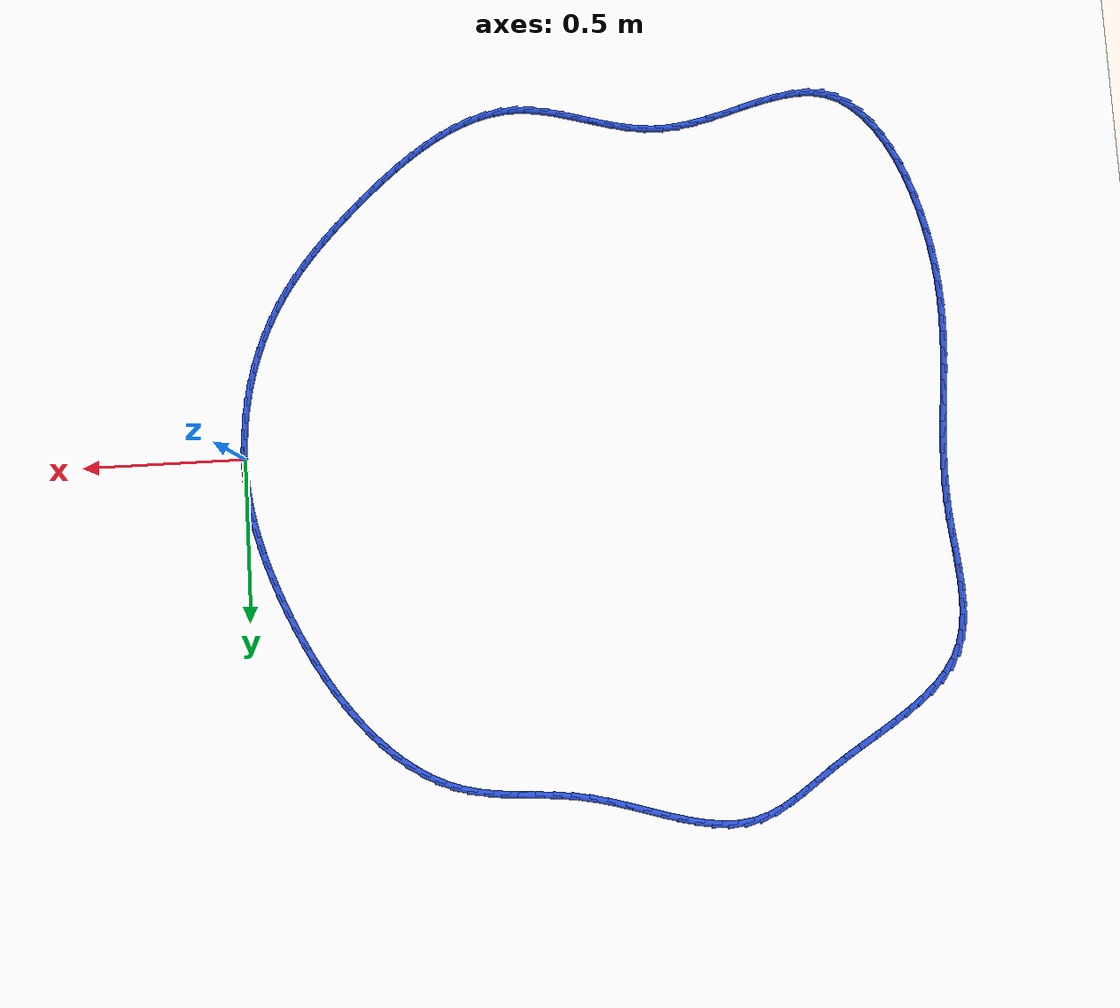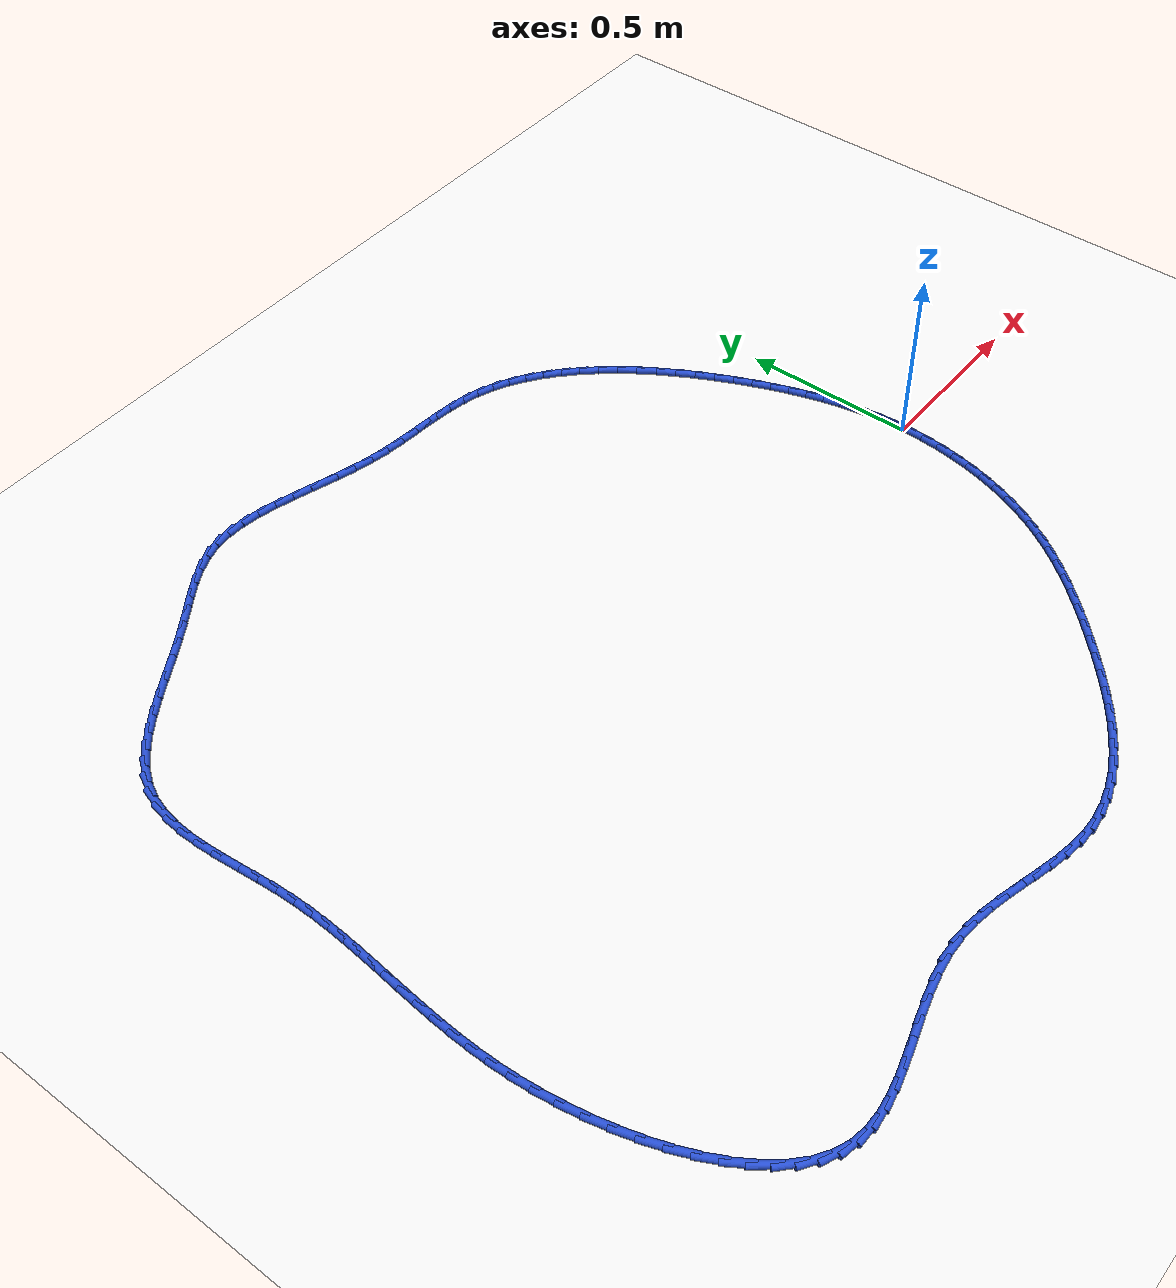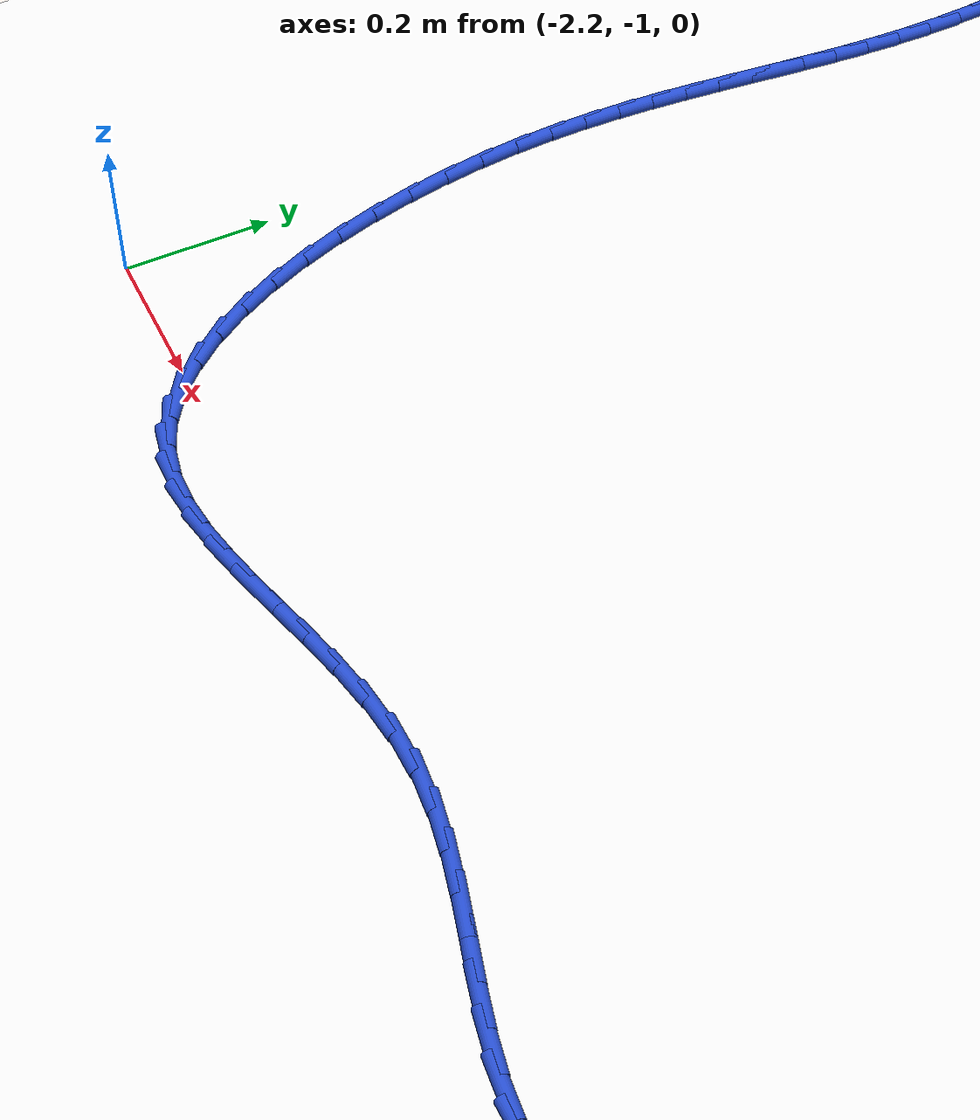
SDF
<sdf version="1.6">
 <world name="default">
  <light name="sun" type="directional">
   <pose>0 0 10 0 -0 0</pose>
   <diffuse>0.8 0.8 0.8 1</diffuse>
   <specular>0.2 0.2 0.2 1</specular>
   <attenuation>
    <range>1000</range>
    <constant>0.9</constant>
    <linear>0.01</linear>
    <quadratic>0.001</quadratic>
   </attenuation>
   <direction>-0.5 0.1 -0.9</direction>
  </light>
  <model name="ground_plane">
   <static>1</static>
   <link name="link">
    <collision name="collision">
     <geometry><plane><normal>0 0 1</normal><size>100 100</size></plane></geometry>
     <surface><friction><ode><mu>100</mu><mu2>50</mu2></ode></friction></surface>
    </collision>
    <visual name="visual">
     <cast_shadows>0</cast_shadows>
     <geometry><plane><normal>0 0 1</normal><size>100 100</size></plane></geometry>
     <material>
      <script><uri>file://media/materials/scripts/gazebo.material</uri><name>Gazebo/WhiteGlow</name></script>
     </material>
    </visual>
   </link>
  </model>
  <gravity>0 0 -9.8</gravity>
  <magnetic_field>6e-06 2.3e-05 -4.2e-05</magnetic_field>
  <atmosphere type="adiabatic"/>
  <physics name="default_physics" default="0" type="ode">
   <max_step_size>0.001</max_step_size>
   <real_time_factor>1</real_time_factor>
   <real_time_update_rate>1000</real_time_update_rate>
  </physics>
  <scene><ambient>0.4 0.4 0.4 1</ambient><background>0.7 0.7 0.7 1</background><shadows>1</shadows></scene>
  <spherical_coordinates>
   <surface_model>EARTH_WGS84</surface_model>
   <latitude_deg>0</latitude_deg>
   <longitude_deg>0</longitude_deg>
   <elevation>0</elevation>
   <heading_deg>0</heading_deg>
  </spherical_coordinates>
  <model name="line">
   <link name="link_0">
    <pose>5.898059818321144e-17 4.163336342344337e-17 0.01 0 1.57 -1.5320431930649714</pose>
    <collision name="collision">
     <geometry><cylinder><radius>0.01</radius><length>0.08</length></cylinder></geometry>
    </collision>
    <visual name="visual">
     <material>
      <script><name>Gazebo/Blue</name><uri>file://media/materials/scripts/gazebo.material</uri></script>
     </material>
     <geometry><cylinder><radius>0.01</radius><length>0.08</length></cylinder></geometry>
    </visual>
   </link>
   <link name="link_1">
    <pose>-0.0019871399659238563 0.05125121272329926 0.01 0 1.57 -1.4771043415872511</pose>
    <collision name="collision">
     <geometry><cylinder><radius>0.01</radius><length>0.08</length></cylinder></geometry>
    </collision>
    <visual name="visual">
     <material>
      <script><name>Gazebo/Blue</name><uri>file://media/materials/scripts/gazebo.material</uri></script>
     </material>
     <geometry><cylinder><radius>0.01</radius><length>0.08</length></cylinder></geometry>
    </visual>
   </link>
   <link name="link_2">
    <pose>-0.006762058978513102 0.10206600874207374 0.01 0 1.57 -1.424621499859907</pose>
    <collision name="collision">
     <geometry><cylinder><radius>0.01</radius><length>0.08</length></cylinder></geometry>
    </collision>
    <visual name="visual">
     <material>
      <script><name>Gazebo/Blue</name><uri>file://media/materials/scripts/gazebo.material</uri></script>
     </material>
     <geometry><cylinder><radius>0.01</radius><length>0.08</length></cylinder></geometry>
    </visual>
   </link>
   <link name="link_3">
    <pose>-0.014192375530316357 0.1525351611826902 0.01 0 1.57 -1.3751156182954565</pose>
    <collision name="collision">
     <geometry><cylinder><radius>0.01</radius><length>0.08</length></cylinder></geometry>
    </collision>
    <visual name="visual">
     <material>
      <script><name>Gazebo/Blue</name><uri>file://media/materials/scripts/gazebo.material</uri></script>
     </material>
     <geometry><cylinder><radius>0.01</radius><length>0.08</length></cylinder></geometry>
    </visual>
   </link>
   <link name="link_4">
    <pose>-0.02414570811388227 0.20274944317151525 0.01 0 1.57 -1.3289902384310273</pose>
    <collision name="collision">
     <geometry><cylinder><radius>0.01</radius><length>0.08</length></cylinder></geometry>
    </collision>
    <visual name="visual">
     <material>
      <script><name>Gazebo/Blue</name><uri>file://media/materials/scripts/gazebo.material</uri></script>
     </material>
     <geometry><cylinder><radius>0.01</radius><length>0.08</length></cylinder></geometry>
    </visual>
   </link>
   <link name="link_5">
    <pose>-0.03648967522175954 0.25279962783491566 0.01 0 1.57 -1.2865295445331488</pose>
    <collision name="collision">
     <geometry><cylinder><radius>0.01</radius><length>0.08</length></cylinder></geometry>
    </collision>
    <visual name="visual">
     <material>
      <script><name>Gazebo/Blue</name><uri>file://media/materials/scripts/gazebo.material</uri></script>
     </material>
     <geometry><cylinder><radius>0.01</radius><length>0.08</length></cylinder></geometry>
    </visual>
   </link>
   <link name="link_6">
    <pose>-0.05109189534649681 0.30277648829925824 0.01 0 1.57 -1.247906283066447</pose>
    <collision name="collision">
     <geometry><cylinder><radius>0.01</radius><length>0.08</length></cylinder></geometry>
    </collision>
    <visual name="visual">
     <material>
      <script><name>Gazebo/Blue</name><uri>file://media/materials/scripts/gazebo.material</uri></script>
     </material>
     <geometry><cylinder><radius>0.01</radius><length>0.08</length></cylinder></geometry>
    </visual>
   </link>
   <link name="link_7">
    <pose>-0.06781998698064275 0.35277079769090947 0.01 0 1.57 -1.2131962441955746</pose>
    <collision name="collision">
     <geometry><cylinder><radius>0.01</radius><length>0.08</length></cylinder></geometry>
    </collision>
    <visual name="visual">
     <material>
      <script><name>Gazebo/Blue</name><uri>file://media/materials/scripts/gazebo.material</uri></script>
     </material>
     <geometry><cylinder><radius>0.01</radius><length>0.08</length></cylinder></geometry>
    </visual>
   </link>
   <link name="link_8">
    <pose>-0.08654156861674608 0.4028733291362364 0.01 0 1.57 -1.1823477809454601</pose>
    <collision name="collision">
     <geometry><cylinder><radius>0.01</radius><length>0.08</length></cylinder></geometry>
    </collision>
    <visual name="visual">
     <material>
      <script><name>Gazebo/Blue</name><uri>file://media/materials/scripts/gazebo.material</uri></script>
     </material>
     <geometry><cylinder><radius>0.01</radius><length>0.08</length></cylinder></geometry>
    </visual>
   </link>
   <link name="link_9">
    <pose>-0.10712542488319872 0.4531707876500715 0.01 0 1.57 -1.1531765955939826</pose>
    <collision name="collision">
     <geometry><cylinder><radius>0.01</radius><length>0.08</length></cylinder></geometry>
    </collision>
    <visual name="visual">
     <material>
      <script><name>Gazebo/Blue</name><uri>file://media/materials/scripts/gazebo.material</uri></script>
     </material>
     <geometry><cylinder><radius>0.01</radius><length>0.08</length></cylinder></geometry>
    </visual>
   </link>
   <link name="link_10">
    <pose>-0.12949060444019084 0.50357453016181 0.01 0 1.57 -1.1225323568267886</pose>
    <collision name="collision">
     <geometry><cylinder><radius>0.01</radius><length>0.08</length></cylinder></geometry>
    </collision>
    <visual name="visual">
     <material>
      <script><name>Gazebo/Blue</name><uri>file://media/materials/scripts/gazebo.material</uri></script>
     </material>
     <geometry><cylinder><radius>0.01</radius><length>0.08</length></cylinder></geometry>
    </visual>
   </link>
   <link name="link_11">
    <pose>-0.1536244555201996 0.5537576478110093 0.01 0 1.57 -1.0898012316331644</pose>
    <collision name="collision">
     <geometry><cylinder><radius>0.01</radius><length>0.08</length></cylinder></geometry>
    </collision>
    <visual name="visual">
     <material>
      <script><name>Gazebo/Blue</name><uri>file://media/materials/scripts/gazebo.material</uri></script>
     </material>
     <geometry><cylinder><radius>0.01</radius><length>0.08</length></cylinder></geometry>
    </visual>
   </link>
   <link name="link_12">
    <pose>-0.17951920623906803 0.6033762080689149 0.01 0 1.57 -1.0545404654575479</pose>
    <collision name="collision">
     <geometry><cylinder><radius>0.01</radius><length>0.08</length></cylinder></geometry>
    </collision>
    <visual name="visual">
     <material>
      <script><name>Gazebo/Blue</name><uri>file://media/materials/scripts/gazebo.material</uri></script>
     </material>
     <geometry><cylinder><radius>0.01</radius><length>0.08</length></cylinder></geometry>
    </visual>
   </link>
   <link name="link_13">
    <pose>-0.207167084712639 0.6520862784067722 0.01 0 1.57 -1.016265073724541</pose>
    <collision name="collision">
     <geometry><cylinder><radius>0.01</radius><length>0.08</length></cylinder></geometry>
    </collision>
    <visual name="visual">
     <material>
      <script><name>Gazebo/Blue</name><uri>file://media/materials/scripts/gazebo.material</uri></script>
     </material>
     <geometry><cylinder><radius>0.01</radius><length>0.08</length></cylinder></geometry>
    </visual>
   </link>
   <link name="link_14">
    <pose>-0.23656031905675562 0.6995439262958266 0.01 0 1.57 -0.9744381176498755</pose>
    <collision name="collision">
     <geometry><cylinder><radius>0.01</radius><length>0.08</length></cylinder></geometry>
    </collision>
    <visual name="visual">
     <material>
      <script><name>Gazebo/Blue</name><uri>file://media/materials/scripts/gazebo.material</uri></script>
     </material>
     <geometry><cylinder><radius>0.01</radius><length>0.08</length></cylinder></geometry>
    </visual>
   </link>
   <link name="link_15">
    <pose>-0.2676911373872609 0.7454052192073238 0.01 0 1.57 -0.9284637713056544</pose>
    <collision name="collision">
     <geometry><cylinder><radius>0.01</radius><length>0.08</length></cylinder></geometry>
    </collision>
    <visual name="visual">
     <material>
      <script><name>Gazebo/Blue</name><uri>file://media/materials/scripts/gazebo.material</uri></script>
     </material>
     <geometry><cylinder><radius>0.01</radius><length>0.08</length></cylinder></geometry>
    </visual>
   </link>
   <link name="link_16">
    <pose>-0.30055176781999776 0.7893262246125089 0.01 0 1.57 -0.8776853203044113</pose>
    <collision name="collision">
     <geometry><cylinder><radius>0.01</radius><length>0.08</length></cylinder></geometry>
    </collision>
    <visual name="visual">
     <material>
      <script><name>Gazebo/Blue</name><uri>file://media/materials/scripts/gazebo.material</uri></script>
     </material>
     <geometry><cylinder><radius>0.01</radius><length>0.08</length></cylinder></geometry>
    </visual>
   </link>
   <link name="link_17">
    <pose>-0.33513443847080926 0.8309630099826275 0.01 0 1.57 -0.8213918172160843</pose>
    <collision name="collision">
     <geometry><cylinder><radius>0.01</radius><length>0.08</length></cylinder></geometry>
    </collision>
    <visual name="visual">
     <material>
      <script><name>Gazebo/Blue</name><uri>file://media/materials/scripts/gazebo.material</uri></script>
     </material>
     <geometry><cylinder><radius>0.01</radius><length>0.08</length></cylinder></geometry>
    </visual>
   </link>
   <link name="link_18">
    <pose>-0.3714313774555384 0.8699716427889256 0.01 0 1.57 -0.7588391995971175</pose>
    <collision name="collision">
     <geometry><cylinder><radius>0.01</radius><length>0.08</length></cylinder></geometry>
    </collision>
    <visual name="visual">
     <material>
      <script><name>Gazebo/Blue</name><uri>file://media/materials/scripts/gazebo.material</uri></script>
     </material>
     <geometry><cylinder><radius>0.01</radius><length>0.08</length></cylinder></geometry>
    </visual>
   </link>
   <link name="link_19">
    <pose>-0.4094348128900281 0.9060081905026476 0.01 0 1.57 -0.6892939933583188</pose>
    <collision name="collision">
     <geometry><cylinder><radius>0.01</radius><length>0.08</length></cylinder></geometry>
    </collision>
    <visual name="visual">
     <material>
      <script><name>Gazebo/Blue</name><uri>file://media/materials/scripts/gazebo.material</uri></script>
     </material>
     <geometry><cylinder><radius>0.01</radius><length>0.08</length></cylinder></geometry>
    </visual>
   </link>
   <link name="link_20">
    <pose>-0.4491369728901214 0.9387287205950393 0.01 0 1.57 -0.6121093011236176</pose>
    <collision name="collision">
     <geometry><cylinder><radius>0.01</radius><length>0.08</length></cylinder></geometry>
    </collision>
    <visual name="visual">
     <material>
      <script><name>Gazebo/Blue</name><uri>file://media/materials/scripts/gazebo.material</uri></script>
     </material>
     <geometry><cylinder><radius>0.01</radius><length>0.08</length></cylinder></geometry>
    </visual>
   </link>
   <link name="link_21">
    <pose>-0.4905300855716615 0.9677893005373466 0.01 0 1.57 -0.526841353721841</pose>
    <collision name="collision">
     <geometry><cylinder><radius>0.01</radius><length>0.08</length></cylinder></geometry>
    </collision>
    <visual name="visual">
     <material>
      <script><name>Gazebo/Blue</name><uri>file://media/materials/scripts/gazebo.material</uri></script>
     </material>
     <geometry><cylinder><radius>0.01</radius><length>0.08</length></cylinder></geometry>
    </visual>
   </link>
   <link name="link_22">
    <pose>-0.533606379050491 0.9928459978008146 0.01 0 1.57 -0.43340668030770224</pose>
    <collision name="collision">
     <geometry><cylinder><radius>0.01</radius><length>0.08</length></cylinder></geometry>
    </collision>
    <visual name="visual">
     <material>
      <script><name>Gazebo/Blue</name><uri>file://media/materials/scripts/gazebo.material</uri></script>
     </material>
     <geometry><cylinder><radius>0.01</radius><length>0.08</length></cylinder></geometry>
    </visual>
   </link>
   <link name="link_23">
    <pose>-0.5783580814424532 1.013554879856689 0.01 0 1.57 -0.332260951024081</pose>
    <collision name="collision">
     <geometry><cylinder><radius>0.01</radius><length>0.08</length></cylinder></geometry>
    </collision>
    <visual name="visual">
     <material>
      <script><name>Gazebo/Blue</name><uri>file://media/materials/scripts/gazebo.material</uri></script>
     </material>
     <geometry><cylinder><radius>0.01</radius><length>0.08</length></cylinder></geometry>
    </visual>
   </link>
   <link name="link_24">
    <pose>-0.6247774208633909 1.0295720141762144 0.01 0 1.57 -0.22993582774793728</pose>
    <collision name="collision">
     <geometry><cylinder><radius>0.01</radius><length>0.08</length></cylinder></geometry>
    </collision>
    <visual name="visual">
     <material>
      <script><name>Gazebo/Blue</name><uri>file://media/materials/scripts/gazebo.material</uri></script>
     </material>
     <geometry><cylinder><radius>0.01</radius><length>0.08</length></cylinder></geometry>
    </visual>
   </link>
   <link name="link_25">
    <pose>-0.6728209117523835 1.040817826639021 0.01 0 1.57 -0.14973775238715487</pose>
    <collision name="collision">
     <geometry><cylinder><radius>0.01</radius><length>0.08</length></cylinder></geometry>
    </collision>
    <visual name="visual">
     <material>
      <script><name>Gazebo/Blue</name><uri>file://media/materials/scripts/gazebo.material</uri></script>
     </material>
     <geometry><cylinder><radius>0.01</radius><length>0.08</length></cylinder></geometry>
    </visual>
   </link>
   <link name="link_26">
    <pose>-0.7223005264348741 1.0482826672145227 0.01 0 1.57 -0.09724110592672376</pose>
    <collision name="collision">
     <geometry><cylinder><radius>0.01</radius><length>0.08</length></cylinder></geometry>
    </collision>
    <visual name="visual">
     <material>
      <script><name>Gazebo/Blue</name><uri>file://media/materials/scripts/gazebo.material</uri></script>
     </material>
     <geometry><cylinder><radius>0.01</radius><length>0.08</length></cylinder></geometry>
    </visual>
   </link>
   <link name="link_27">
    <pose>-0.7729916748852738 1.0532275263046458 0.01 0 1.57 -0.0712030340251287</pose>
    <collision name="collision">
     <geometry><cylinder><radius>0.01</radius><length>0.08</length></cylinder></geometry>
    </collision>
    <visual name="visual">
     <material>
      <script><name>Gazebo/Blue</name><uri>file://media/materials/scripts/gazebo.material</uri></script>
     </material>
     <geometry><cylinder><radius>0.01</radius><length>0.08</length></cylinder></geometry>
    </visual>
   </link>
   <link name="link_28">
    <pose>-0.8246697670758255 1.0569133943273572 0.01 0 1.57 -0.07020927702640174</pose>
    <collision name="collision">
     <geometry><cylinder><radius>0.01</radius><length>0.08</length></cylinder></geometry>
    </collision>
    <visual name="visual">
     <material>
      <script><name>Gazebo/Blue</name><uri>file://media/materials/scripts/gazebo.material</uri></script>
     </material>
     <geometry><cylinder><radius>0.01</radius><length>0.08</length></cylinder></geometry>
    </visual>
   </link>
   <link name="link_29">
    <pose>-0.877110212978773 1.0606012617006242 0.01 0 1.57 -0.09318019977965995</pose>
    <collision name="collision">
     <geometry><cylinder><radius>0.01</radius><length>0.08</length></cylinder></geometry>
    </collision>
    <visual name="visual">
     <material>
      <script><name>Gazebo/Blue</name><uri>file://media/materials/scripts/gazebo.material</uri></script>
     </material>
     <geometry><cylinder><radius>0.01</radius><length>0.08</length></cylinder></geometry>
    </visual>
   </link>
   <link name="link_30">
    <pose>-0.9300884225663593 1.0655521188424144 0.01 0 1.57 -0.13935439247038758</pose>
    <collision name="collision">
     <geometry><cylinder><radius>0.01</radius><length>0.08</length></cylinder></geometry>
    </collision>
    <visual name="visual">
     <material>
      <script><name>Gazebo/Blue</name><uri>file://media/materials/scripts/gazebo.material</uri></script>
     </material>
     <geometry><cylinder><radius>0.01</radius><length>0.08</length></cylinder></geometry>
    </visual>
   </link>
   <link name="link_31">
    <pose>-0.9833798058108274 1.0730269561706942 0.01 0 1.57 -0.20276946579564908</pose>
    <collision name="collision">
     <geometry><cylinder><radius>0.01</radius><length>0.08</length></cylinder></geometry>
    </collision>
    <visual name="visual">
     <material>
      <script><name>Gazebo/Blue</name><uri>file://media/materials/scripts/gazebo.material</uri></script>
     </material>
     <geometry><cylinder><radius>0.01</radius><length>0.08</length></cylinder></geometry>
    </visual>
   </link>
   <link name="link_32">
    <pose>-1.0367667210239564 1.0840030352330565 0.01 0 1.57 -0.25405035956417626</pose>
    <collision name="collision">
     <geometry><cylinder><radius>0.01</radius><length>0.08</length></cylinder></geometry>
    </collision>
    <visual name="visual">
     <material>
      <script><name>Gazebo/Blue</name><uri>file://media/materials/scripts/gazebo.material</uri></script>
     </material>
     <geometry><cylinder><radius>0.01</radius><length>0.08</length></cylinder></geometry>
    </visual>
   </link>
   <link name="link_33">
    <pose>-1.0900710410163217 1.097844080407512 0.01 0 1.57 -0.2842284866814885</pose>
    <collision name="collision">
     <geometry><cylinder><radius>0.01</radius><length>0.08</length></cylinder></geometry>
    </collision>
    <visual name="visual">
     <material>
      <script><name>Gazebo/Blue</name><uri>file://media/materials/scripts/gazebo.material</uri></script>
     </material>
     <geometry><cylinder><radius>0.01</radius><length>0.08</length></cylinder></geometry>
    </visual>
   </link>
   <link name="link_34">
    <pose>-1.1431285879127984 1.1133442090214982 0.01 0 1.57 -0.2942199927335228</pose>
    <collision name="collision">
     <geometry><cylinder><radius>0.01</radius><length>0.08</length></cylinder></geometry>
    </collision>
    <visual name="visual">
     <material>
      <script><name>Gazebo/Blue</name><uri>file://media/materials/scripts/gazebo.material</uri></script>
     </material>
     <geometry><cylinder><radius>0.01</radius><length>0.08</length></cylinder></geometry>
    </visual>
   </link>
   <link name="link_35">
    <pose>-1.1957751997143389 1.1292968901179297 0.01 0 1.57 -0.2839919253931296</pose>
    <collision name="collision">
     <geometry><cylinder><radius>0.01</radius><length>0.08</length></cylinder></geometry>
    </collision>
    <visual name="visual">
     <material>
      <script><name>Gazebo/Blue</name><uri>file://media/materials/scripts/gazebo.material</uri></script>
     </material>
     <geometry><cylinder><radius>0.01</radius><length>0.08</length></cylinder></geometry>
    </visual>
   </link>
   <link name="link_36">
    <pose>-1.2478467144218943 1.1444955927397207 0.01 0 1.57 -0.25239280091441885</pose>
    <collision name="collision">
     <geometry><cylinder><radius>0.01</radius><length>0.08</length></cylinder></geometry>
    </collision>
    <visual name="visual">
     <material>
      <script><name>Gazebo/Blue</name><uri>file://media/materials/scripts/gazebo.material</uri></script>
     </material>
     <geometry><cylinder><radius>0.01</radius><length>0.08</length></cylinder></geometry>
    </visual>
   </link>
   <link name="link_37">
    <pose>-1.2991789700364174 1.1577337859297863 0.01 0 1.57 -0.1971168937796746</pose>
    <collision name="collision">
     <geometry><cylinder><radius>0.01</radius><length>0.08</length></cylinder></geometry>
    </collision>
    <visual name="visual">
     <material>
      <script><name>Gazebo/Blue</name><uri>file://media/materials/scripts/gazebo.material</uri></script>
     </material>
     <geometry><cylinder><radius>0.01</radius><length>0.08</length></cylinder></geometry>
    </visual>
   </link>
   <link name="link_38">
    <pose>-1.3496078045588575 1.1678049387310399 0.01 0 1.57 -0.11491763898033701</pose>
    <collision name="collision">
     <geometry><cylinder><radius>0.01</radius><length>0.08</length></cylinder></geometry>
    </collision>
    <visual name="visual">
     <material>
      <script><name>Gazebo/Blue</name><uri>file://media/materials/scripts/gazebo.material</uri></script>
     </material>
     <geometry><cylinder><radius>0.01</radius><length>0.08</length></cylinder></geometry>
    </visual>
   </link>
   <link name="link_39">
    <pose>-1.3989690559901689 1.1735025201863962 0.01 0 1.57 -0.0024408918352235385</pose>
    <collision name="collision">
     <geometry><cylinder><radius>0.01</radius><length>0.08</length></cylinder></geometry>
    </collision>
    <visual name="visual">
     <material>
      <script><name>Gazebo/Blue</name><uri>file://media/materials/scripts/gazebo.material</uri></script>
     </material>
     <geometry><cylinder><radius>0.01</radius><length>0.08</length></cylinder></geometry>
    </visual>
   </link>
   <link name="link_40">
    <pose>-1.4470985623313013 1.1736199993387695 0.01 0 1.57 0.1417487027392468</pose>
    <collision name="collision">
     <geometry><cylinder><radius>0.01</radius><length>0.08</length></cylinder></geometry>
    </collision>
    <visual name="visual">
     <material>
      <script><name>Gazebo/Blue</name><uri>file://media/materials/scripts/gazebo.material</uri></script>
     </material>
     <geometry><cylinder><radius>0.01</radius><length>0.08</length></cylinder></geometry>
    </visual>
   </link>
   <link name="link_41">
    <pose>-1.4938321615832073 1.1669508452310737 0.01 0 1.57 0.30954262503907953</pose>
    <collision name="collision">
     <geometry><cylinder><radius>0.01</radius><length>0.08</length></cylinder></geometry>
    </collision>
    <visual name="visual">
     <material>
      <script><name>Gazebo/Blue</name><uri>file://media/materials/scripts/gazebo.material</uri></script>
     </material>
     <geometry><cylinder><radius>0.01</radius><length>0.08</length></cylinder></geometry>
    </visual>
   </link>
   <link name="link_42">
    <pose>-1.5390575189143194 1.1524867234338771 0.01 0 1.57 0.4533053883004914</pose>
    <collision name="collision">
     <geometry><cylinder><radius>0.01</radius><length>0.08</length></cylinder></geometry>
    </collision>
    <visual name="visual">
     <material>
      <script><name>Gazebo/Blue</name><uri>file://media/materials/scripts/gazebo.material</uri></script>
     </material>
     <geometry><cylinder><radius>0.01</radius><length>0.08</length></cylinder></geometry>
    </visual>
   </link>
   <link name="link_43">
    <pose>-1.5831321941276177 1.1310162621814484 0.01 0 1.57 0.5507011513820227</pose>
    <collision name="collision">
     <geometry><cylinder><radius>0.01</radius><length>0.08</length></cylinder></geometry>
    </collision>
    <visual name="visual">
     <material>
      <script><name>Gazebo/Blue</name><uri>file://media/materials/scripts/gazebo.material</uri></script>
     </material>
     <geometry><cylinder><radius>0.01</radius><length>0.08</length></cylinder></geometry>
    </visual>
   </link>
   <link name="link_44">
    <pose>-1.6266639028088785 1.1042847309819646 0.01 0 1.57 0.6063917639440316</pose>
    <collision name="collision">
     <geometry><cylinder><radius>0.01</radius><length>0.08</length></cylinder></geometry>
    </collision>
    <visual name="visual">
     <material>
      <script><name>Gazebo/Blue</name><uri>file://media/materials/scripts/gazebo.material</uri></script>
     </material>
     <geometry><cylinder><radius>0.01</radius><length>0.08</length></cylinder></geometry>
    </visual>
   </link>
   <link name="link_45">
    <pose>-1.6702626859289698 1.0740462920397138 0.01 0 1.57 0.6256949915375298</pose>
    <collision name="collision">
     <geometry><cylinder><radius>0.01</radius><length>0.08</length></cylinder></geometry>
    </collision>
    <visual name="visual">
     <material>
      <script><name>Gazebo/Blue</name><uri>file://media/materials/scripts/gazebo.material</uri></script>
     </material>
     <geometry><cylinder><radius>0.01</radius><length>0.08</length></cylinder></geometry>
    </visual>
   </link>
   <link name="link_46">
    <pose>-1.7145385844587604 1.0420551075589826 0.01 0 1.57 0.6122013956370432</pose>
    <collision name="collision">
     <geometry><cylinder><radius>0.01</radius><length>0.08</length></cylinder></geometry>
    </collision>
    <visual name="visual">
     <material>
      <script><name>Gazebo/Blue</name><uri>file://media/materials/scripts/gazebo.material</uri></script>
     </material>
     <geometry><cylinder><radius>0.01</radius><length>0.08</length></cylinder></geometry>
    </visual>
   </link>
   <link name="link_47">
    <pose>-1.7600995076961947 1.010062196872103 0.01 0 1.57 0.5812556445735787</pose>
    <collision name="collision">
     <geometry><cylinder><radius>0.01</radius><length>0.08</length></cylinder></geometry>
    </collision>
    <visual name="visual">
     <material>
      <script><name>Gazebo/Blue</name><uri>file://media/materials/scripts/gazebo.material</uri></script>
     </material>
     <geometry><cylinder><radius>0.01</radius><length>0.08</length></cylinder></geometry>
    </visual>
   </link>
   <link name="link_48">
    <pose>-1.8071161341715574 0.9791739399284247 0.01 0 1.57 0.563237297716324</pose>
    <collision name="collision">
     <geometry><cylinder><radius>0.01</radius><length>0.08</length></cylinder></geometry>
    </collision>
    <visual name="visual">
     <material>
      <script><name>Gazebo/Blue</name><uri>file://media/materials/scripts/gazebo.material</uri></script>
     </material>
     <geometry><cylinder><radius>0.01</radius><length>0.08</length></cylinder></geometry>
    </visual>
   </link>
   <link name="link_49">
    <pose>-1.8547907372028265 0.9490689302891719 0.01 0 1.57 0.5617282108317725</pose>
    <collision name="collision">
     <geometry><cylinder><radius>0.01</radius><length>0.08</length></cylinder></geometry>
    </collision>
    <visual name="visual">
     <material>
      <script><name>Gazebo/Blue</name><uri>file://media/materials/scripts/gazebo.material</uri></script>
     </material>
     <geometry><cylinder><radius>0.01</radius><length>0.08</length></cylinder></geometry>
    </visual>
   </link>
   <link name="link_50">
    <pose>-1.9021956540900211 0.9192341879104146 0.01 0 1.57 0.577022077002782</pose>
    <collision name="collision">
     <geometry><cylinder><radius>0.01</radius><length>0.08</length></cylinder></geometry>
    </collision>
    <visual name="visual">
     <material>
      <script><name>Gazebo/Blue</name><uri>file://media/materials/scripts/gazebo.material</uri></script>
     </material>
     <geometry><cylinder><radius>0.01</radius><length>0.08</length></cylinder></geometry>
    </visual>
   </link>
   <link name="link_51">
    <pose>-1.9484032221331598 0.8891567327482232 0.01 0 1.57 0.6103507070461927</pose>
    <collision name="collision">
     <geometry><cylinder><radius>0.01</radius><length>0.08</length></cylinder></geometry>
    </collision>
    <visual name="visual">
     <material>
      <script><name>Gazebo/Blue</name><uri>file://media/materials/scripts/gazebo.material</uri></script>
     </material>
     <geometry><cylinder><radius>0.01</radius><length>0.08</length></cylinder></geometry>
    </visual>
   </link>
   <link name="link_52">
    <pose>-1.9924857786322612 0.858323584758668 0.01 0 1.57 0.6639173437627273</pose>
    <collision name="collision">
     <geometry><cylinder><radius>0.01</radius><length>0.08</length></cylinder></geometry>
    </collision>
    <visual name="visual">
     <material>
      <script><name>Gazebo/Blue</name><uri>file://media/materials/scripts/gazebo.material</uri></script>
     </material>
     <geometry><cylinder><radius>0.01</radius><length>0.08</length></cylinder></geometry>
    </visual>
   </link>
   <link name="link_53">
    <pose>-2.033515660887343 0.8262217638978193 0.01 0 1.57 0.7407931043346598</pose>
    <collision name="collision">
     <geometry><cylinder><radius>0.01</radius><length>0.08</length></cylinder></geometry>
    </collision>
    <visual name="visual">
     <material>
      <script><name>Gazebo/Blue</name><uri>file://media/materials/scripts/gazebo.material</uri></script>
     </material>
     <geometry><cylinder><radius>0.01</radius><length>0.08</length></cylinder></geometry>
    </visual>
   </link>
   <link name="link_54">
    <pose>-2.0705652061984257 0.7923382901217476 0.01 0 1.57 0.8444130108672926</pose>
    <collision name="collision">
     <geometry><cylinder><radius>0.01</radius><length>0.08</length></cylinder></geometry>
    </collision>
    <visual name="visual">
     <material>
      <script><name>Gazebo/Blue</name><uri>file://media/materials/scripts/gazebo.material</uri></script>
     </material>
     <geometry><cylinder><radius>0.01</radius><length>0.08</length></cylinder></geometry>
    </visual>
   </link>
   <link name="link_55">
    <pose>-2.102706751865526 0.7561601833865226 0.01 0 1.57 0.9772136874753343</pose>
    <collision name="collision">
     <geometry><cylinder><radius>0.01</radius><length>0.08</length></cylinder></geometry>
    </collision>
    <visual name="visual">
     <material>
      <script><name>Gazebo/Blue</name><uri>file://media/materials/scripts/gazebo.material</uri></script>
     </material>
     <geometry><cylinder><radius>0.01</radius><length>0.08</length></cylinder></geometry>
    </visual>
   </link>
   <link name="link_56">
    <pose>-2.129012635188664 0.7171744636482156 0.01 0 1.57 1.1379415217152118</pose>
    <collision name="collision">
     <geometry><cylinder><radius>0.01</radius><length>0.08</length></cylinder></geometry>
    </collision>
    <visual name="visual">
     <material>
      <script><name>Gazebo/Blue</name><uri>file://media/materials/scripts/gazebo.material</uri></script>
     </material>
     <geometry><cylinder><radius>0.01</radius><length>0.08</length></cylinder></geometry>
    </visual>
   </link>
   <link name="link_57">
    <pose>-2.1485603280377905 0.6748708413036107 0.01 0 1.57 1.3036612683069253</pose>
    <collision name="collision">
     <geometry><cylinder><radius>0.01</radius><length>0.08</length></cylinder></geometry>
    </collision>
    <visual name="visual">
     <material>
      <script><name>Gazebo/Blue</name><uri>file://media/materials/scripts/gazebo.material</uri></script>
     </material>
     <geometry><cylinder><radius>0.01</radius><length>0.08</length></cylinder></geometry>
    </visual>
   </link>
   <link name="link_58">
    <pose>-2.161090415264759 0.6290864884041797 0.01 0 1.57 1.4369293011359263</pose>
    <collision name="collision">
     <geometry><cylinder><radius>0.01</radius><length>0.08</length></cylinder></geometry>
    </collision>
    <visual name="visual">
     <material>
      <script><name>Gazebo/Blue</name><uri>file://media/materials/scripts/gazebo.material</uri></script>
     </material>
     <geometry><cylinder><radius>0.01</radius><length>0.08</length></cylinder></geometry>
    </visual>
   </link>
   <link name="link_59">
    <pose>-2.1676544806320344 0.580345521554137 0.01 0 1.57 1.535511839931679</pose>
    <collision name="collision">
     <geometry><cylinder><radius>0.01</radius><length>0.08</length></cylinder></geometry>
    </collision>
    <visual name="visual">
     <material>
      <script><name>Gazebo/Blue</name><uri>file://media/materials/scripts/gazebo.material</uri></script>
     </material>
     <geometry><cylinder><radius>0.01</radius><length>0.08</length></cylinder></geometry>
    </visual>
   </link>
   <link name="link_60">
    <pose>-2.1694580130964303 0.529252701463535 0.01 0 1.57 -1.537660950106746</pose>
    <collision name="collision">
     <geometry><cylinder><radius>0.01</radius><length>0.08</length></cylinder></geometry>
    </collision>
    <visual name="visual">
     <material>
      <script><name>Gazebo/Blue</name><uri>file://media/materials/scripts/gazebo.material</uri></script>
     </material>
     <geometry><cylinder><radius>0.01</radius><length>0.08</length></cylinder></geometry>
    </visual>
   </link>
   <link name="link_61">
    <pose>-2.167706501614763 0.476412788842425 0.01 0 1.57 -1.4949713236045996</pose>
    <collision name="collision">
     <geometry><cylinder><radius>0.01</radius><length>0.08</length></cylinder></geometry>
    </collision>
    <visual name="visual">
     <material>
      <script><name>Gazebo/Blue</name><uri>file://media/materials/scripts/gazebo.material</uri></script>
     </material>
     <geometry><cylinder><radius>0.01</radius><length>0.08</length></cylinder></geometry>
    </visual>
   </link>
   <link name="link_62">
    <pose>-2.163605435143847 0.42243054440085975 0.01 0 1.57 -1.4748855197109165</pose>
    <collision name="collision">
     <geometry><cylinder><radius>0.01</radius><length>0.08</length></cylinder></geometry>
    </collision>
    <visual name="visual">
     <material>
      <script><name>Gazebo/Blue</name><uri>file://media/materials/scripts/gazebo.material</uri></script>
     </material>
     <geometry><cylinder><radius>0.01</radius><length>0.08</length></cylinder></geometry>
    </visual>
   </link>
   <link name="link_63">
    <pose>-2.1583603026404985 0.36791072884889015 0.01 0 1.57 -1.4758856568263394</pose>
    <collision name="collision">
     <geometry><cylinder><radius>0.01</radius><length>0.08</length></cylinder></geometry>
    </collision>
    <visual name="visual">
     <material>
      <script><name>Gazebo/Blue</name><uri>file://media/materials/scripts/gazebo.material</uri></script>
     </material>
     <geometry><cylinder><radius>0.01</radius><length>0.08</length></cylinder></geometry>
    </visual>
   </link>
   <link name="link_64">
    <pose>-2.153176593061532 0.31345810289656906 0.01 0 1.57 -1.4980943034781522</pose>
    <collision name="collision">
     <geometry><cylinder><radius>0.01</radius><length>0.08</length></cylinder></geometry>
    </collision>
    <visual name="visual">
     <material>
      <script><name>Gazebo/Blue</name><uri>file://media/materials/scripts/gazebo.material</uri></script>
     </material>
     <geometry><cylinder><radius>0.01</radius><length>0.08</length></cylinder></geometry>
    </visual>
   </link>
   <link name="link_65">
    <pose>-2.149259722980619 0.2596773896866823 0.01 0 1.57 -1.537405648284569</pose>
    <collision name="collision">
     <geometry><cylinder><radius>0.01</radius><length>0.08</length></cylinder></geometry>
    </collision>
    <visual name="visual">
     <material>
      <script><name>Gazebo/Blue</name><uri>file://media/materials/scripts/gazebo.material</uri></script>
     </material>
     <geometry><cylinder><radius>0.01</radius><length>0.08</length></cylinder></geometry>
    </visual>
   </link>
   <link name="link_66">
    <pose>-2.147500469662055 0.2070100127628016 0.01 0 1.57 1.5658890207305909</pose>
    <collision name="collision">
     <geometry><cylinder><radius>0.01</radius><length>0.08</length></cylinder></geometry>
    </collision>
    <visual name="visual">
     <material>
      <script><name>Gazebo/Blue</name><uri>file://media/materials/scripts/gazebo.material</uri></script>
     </material>
     <geometry><cylinder><radius>0.01</radius><length>0.08</length></cylinder></geometry>
    </visual>
   </link>
   <link name="link_67">
    <pose>-2.147753934735375 0.15535987409686777 0.01 0 1.57 1.5332741672964298</pose>
    <collision name="collision">
     <geometry><cylinder><radius>0.01</radius><length>0.08</length></cylinder></geometry>
    </collision>
    <visual name="visual">
     <material>
      <script><name>Gazebo/Blue</name><uri>file://media/materials/scripts/gazebo.material</uri></script>
     </material>
     <geometry><cylinder><radius>0.01</radius><length>0.08</length></cylinder></geometry>
    </visual>
   </link>
   <link name="link_68">
    <pose>-2.1496624358583176 0.10452043956374563 0.01 0 1.57 1.507065928960408</pose>
    <collision name="collision">
     <geometry><cylinder><radius>0.01</radius><length>0.08</length></cylinder></geometry>
    </collision>
    <visual name="visual">
     <material>
      <script><name>Gazebo/Blue</name><uri>file://media/materials/scripts/gazebo.material</uri></script>
     </material>
     <geometry><cylinder><radius>0.01</radius><length>0.08</length></cylinder></geometry>
    </visual>
   </link>
   <link name="link_69">
    <pose>-2.15286829068862 0.05428517503830164 0.01 0 1.57 1.4878067301467068</pose>
    <collision name="collision">
     <geometry><cylinder><radius>0.01</radius><length>0.08</length></cylinder></geometry>
    </collision>
    <visual name="visual">
     <material>
      <script><name>Gazebo/Blue</name><uri>file://media/materials/scripts/gazebo.material</uri></script>
     </material>
     <geometry><cylinder><radius>0.01</radius><length>0.08</length></cylinder></geometry>
    </visual>
   </link>
   <link name="link_70">
    <pose>-2.1570138168840223 0.004447546395400693 0.01 0 1.57 1.475859101177599</pose>
    <collision name="collision">
     <geometry><cylinder><radius>0.01</radius><length>0.08</length></cylinder></geometry>
    </collision>
    <visual name="visual">
     <material>
      <script><name>Gazebo/Blue</name><uri>file://media/materials/scripts/gazebo.material</uri></script>
     </material>
     <geometry><cylinder><radius>0.01</radius><length>0.08</length></cylinder></geometry>
    </visual>
   </link>
   <link name="link_71">
    <pose>-2.1617413321022623 -0.04519898049009072 0.01 0 1.57 1.471414254154546</pose>
    <collision name="collision">
     <geometry><cylinder><radius>0.01</radius><length>0.08</length></cylinder></geometry>
    </collision>
    <visual name="visual">
     <material>
      <script><name>Gazebo/Blue</name><uri>file://media/materials/scripts/gazebo.material</uri></script>
     </material>
     <geometry><cylinder><radius>0.01</radius><length>0.08</length></cylinder></geometry>
    </visual>
   </link>
   <link name="link_72">
    <pose>-2.1666931540010785 -0.09486093974330734 0.01 0 1.57 1.4745019042868728</pose>
    <collision name="collision">
     <geometry><cylinder><radius>0.01</radius><length>0.08</length></cylinder></geometry>
    </collision>
    <visual name="visual">
     <material>
      <script><name>Gazebo/Blue</name><uri>file://media/materials/scripts/gazebo.material</uri></script>
     </material>
     <geometry><cylinder><radius>0.01</radius><length>0.08</length></cylinder></geometry>
    </visual>
   </link>
   <link name="link_73">
    <pose>-2.1715116002382095 -0.14474486548938434 0.01 0 1.57 1.484997158584502</pose>
    <collision name="collision">
     <geometry><cylinder><radius>0.01</radius><length>0.08</length></cylinder></geometry>
    </collision>
    <visual name="visual">
     <material>
      <script><name>Gazebo/Blue</name><uri>file://media/materials/scripts/gazebo.material</uri></script>
     </material>
     <geometry><cylinder><radius>0.01</radius><length>0.08</length></cylinder></geometry>
    </visual>
   </link>
   <link name="link_74">
    <pose>-2.1758389884713933 -0.19505729185345438 0.01 0 1.57 1.5026230161068281</pose>
    <collision name="collision">
     <geometry><cylinder><radius>0.01</radius><length>0.08</length></cylinder></geometry>
    </collision>
    <visual name="visual">
     <material>
      <script><name>Gazebo/Blue</name><uri>file://media/materials/scripts/gazebo.material</uri></script>
     </material>
     <geometry><cylinder><radius>0.01</radius><length>0.08</length></cylinder></geometry>
    </visual>
   </link>
   <link name="link_75">
    <pose>-2.1793176363583706 -0.24600475296065272 0.01 0 1.57 1.5269498040472724</pose>
    <collision name="collision">
     <geometry><cylinder><radius>0.01</radius><length>0.08</length></cylinder></geometry>
    </collision>
    <visual name="visual">
     <material>
      <script><name>Gazebo/Blue</name><uri>file://media/materials/scripts/gazebo.material</uri></script>
     </material>
     <geometry><cylinder><radius>0.01</radius><length>0.08</length></cylinder></geometry>
    </visual>
   </link>
   <link name="link_76">
    <pose>-2.1815898615568763 -0.2977937829361135 0.01 0 1.57 1.557395187540675</pose>
    <collision name="collision">
     <geometry><cylinder><radius>0.01</radius><length>0.08</length></cylinder></geometry>
    </collision>
    <visual name="visual">
     <material>
      <script><name>Gazebo/Blue</name><uri>file://media/materials/scripts/gazebo.material</uri></script>
     </material>
     <geometry><cylinder><radius>0.01</radius><length>0.08</length></cylinder></geometry>
    </visual>
   </link>
   <link name="link_77">
    <pose>-2.182297981724653 -0.3506309159049713 0.01 0 1.57 -1.5483629029984205</pose>
    <collision name="collision">
     <geometry><cylinder><radius>0.01</radius><length>0.08</length></cylinder></geometry>
    </collision>
    <visual name="visual">
     <material>
      <script><name>Gazebo/Blue</name><uri>file://media/materials/scripts/gazebo.material</uri></script>
     </material>
     <geometry><cylinder><radius>0.01</radius><length>0.08</length></cylinder></geometry>
    </visual>
   </link>
   <link name="link_78">
    <pose>-2.181084314519436 -0.4047226859923611 0.01 0 1.57 -1.5079995786750116</pose>
    <collision name="collision">
     <geometry><cylinder><radius>0.01</radius><length>0.08</length></cylinder></geometry>
    </collision>
    <visual name="visual">
     <material>
      <script><name>Gazebo/Blue</name><uri>file://media/materials/scripts/gazebo.material</uri></script>
     </material>
     <geometry><cylinder><radius>0.01</radius><length>0.08</length></cylinder></geometry>
    </visual>
   </link>
   <link name="link_79">
    <pose>-2.1775911775989654 -0.46027562732341565 0.01 0 1.57 -1.4641552264891515</pose>
    <collision name="collision">
     <geometry><cylinder><radius>0.01</radius><length>0.08</length></cylinder></geometry>
    </collision>
    <visual name="visual">
     <material>
      <script><name>Gazebo/Blue</name><uri>file://media/materials/scripts/gazebo.material</uri></script>
     </material>
     <geometry><cylinder><radius>0.01</radius><length>0.08</length></cylinder></geometry>
    </visual>
   </link>
   <link name="link_80">
    <pose>-2.171468237136371 -0.5174741384094412 0.01 0 1.57 -1.4192922191096633</pose>
    <collision name="collision">
     <geometry><cylinder><radius>0.01</radius><length>0.08</length></cylinder></geometry>
    </collision>
    <visual name="visual">
     <material>
      <script><name>Gazebo/Blue</name><uri>file://media/materials/scripts/gazebo.material</uri></script>
     </material>
     <geometry><cylinder><radius>0.01</radius><length>0.08</length></cylinder></geometry>
    </visual>
   </link>
   <link name="link_81">
    <pose>-2.1625335738390645 -0.5759953099730225 0.01 0 1.57 -1.3740965772743556</pose>
    <collision name="collision">
     <geometry><cylinder><radius>0.01</radius><length>0.08</length></cylinder></geometry>
    </collision>
    <visual name="visual">
     <material>
      <script><name>Gazebo/Blue</name><uri>file://media/materials/scripts/gazebo.material</uri></script>
     </material>
     <geometry><cylinder><radius>0.01</radius><length>0.08</length></cylinder></geometry>
    </visual>
   </link>
   <link name="link_82">
    <pose>-2.150773349558047 -0.6350099292063183 0.01 0 1.57 -1.3269714750700436</pose>
    <collision name="collision">
     <geometry><cylinder><radius>0.01</radius><length>0.08</length></cylinder></geometry>
    </collision>
    <visual name="visual">
     <material>
      <script><name>Gazebo/Blue</name><uri>file://media/materials/scripts/gazebo.material</uri></script>
     </material>
     <geometry><cylinder><radius>0.01</radius><length>0.08</length></cylinder></geometry>
    </visual>
   </link>
   <link name="link_83">
    <pose>-2.1361810079814942 -0.6936668485395612 0.01 0 1.57 -1.2762029463363953</pose>
    <collision name="collision">
     <geometry><cylinder><radius>0.01</radius><length>0.08</length></cylinder></geometry>
    </collision>
    <visual name="visual">
     <material>
      <script><name>Gazebo/Blue</name><uri>file://media/materials/scripts/gazebo.material</uri></script>
     </material>
     <geometry><cylinder><radius>0.01</radius><length>0.08</length></cylinder></geometry>
    </visual>
   </link>
   <link name="link_84">
    <pose>-2.1187499927975812 -0.7511149204029871 0.01 0 1.57 -1.2198723062698074</pose>
    <collision name="collision">
     <geometry><cylinder><radius>0.01</radius><length>0.08</length></cylinder></geometry>
    </collision>
    <visual name="visual">
     <material>
      <script><name>Gazebo/Blue</name><uri>file://media/materials/scripts/gazebo.material</uri></script>
     </material>
     <geometry><cylinder><radius>0.01</radius><length>0.08</length></cylinder></geometry>
    </visual>
   </link>
   <link name="link_85">
    <pose>-2.098473747694483 -0.8065029972268307 0.01 0 1.57 -1.1556800622098247</pose>
    <collision name="collision">
     <geometry><cylinder><radius>0.01</radius><length>0.08</length></cylinder></geometry>
    </collision>
    <visual name="visual">
     <material>
      <script><name>Gazebo/Blue</name><uri>file://media/materials/scripts/gazebo.material</uri></script>
     </material>
     <geometry><cylinder><radius>0.01</radius><length>0.08</length></cylinder></geometry>
    </visual>
   </link>
   <link name="link_86">
    <pose>-2.0753457163603732 -0.8589799314413268 0.01 0 1.57 -1.0807554133042194</pose>
    <collision name="collision">
     <geometry><cylinder><radius>0.01</radius><length>0.08</length></cylinder></geometry>
    </collision>
    <visual name="visual">
     <material>
      <script><name>Gazebo/Blue</name><uri>file://media/materials/scripts/gazebo.material</uri></script>
     </material>
     <geometry><cylinder><radius>0.01</radius><length>0.08</length></cylinder></geometry>
    </visual>
   </link>
   <link name="link_87">
    <pose>-2.0493593424834273 -0.9076945754767108 0.01 0 1.57 -0.9914700365448779</pose>
    <collision name="collision">
     <geometry><cylinder><radius>0.01</radius><length>0.08</length></cylinder></geometry>
    </collision>
    <visual name="visual">
     <material>
      <script><name>Gazebo/Blue</name><uri>file://media/materials/scripts/gazebo.material</uri></script>
     </material>
     <geometry><cylinder><radius>0.01</radius><length>0.08</length></cylinder></geometry>
    </visual>
   </link>
   <link name="link_88">
    <pose>-2.020508069751821 -0.9517957817632166 0.01 0 1.57 -0.8833491462353409</pose>
    <collision name="collision">
     <geometry><cylinder><radius>0.01</radius><length>0.08</length></cylinder></geometry>
    </collision>
    <visual name="visual">
     <material>
      <script><name>Gazebo/Blue</name><uri>file://media/materials/scripts/gazebo.material</uri></script>
     </material>
     <geometry><cylinder><radius>0.01</radius><length>0.08</length></cylinder></geometry>
    </visual>
   </link>
   <link name="link_89">
    <pose>-1.988785341853729 -0.9904324027310786 0.01 0 1.57 -0.7513438523489705</pose>
    <collision name="collision">
     <geometry><cylinder><radius>0.01</radius><length>0.08</length></cylinder></geometry>
    </collision>
    <visual name="visual">
     <material>
      <script><name>Gazebo/Blue</name><uri>file://media/materials/scripts/gazebo.material</uri></script>
     </material>
     <geometry><cylinder><radius>0.01</radius><length>0.08</length></cylinder></geometry>
    </visual>
   </link>
   <link name="link_90">
    <pose>-1.9541846024773253 -1.0227532908105323 0.01 0 1.57 -0.5910217430910049</pose>
    <collision name="collision">
     <geometry><cylinder><radius>0.01</radius><length>0.08</length></cylinder></geometry>
    </collision>
    <visual name="visual">
     <material>
      <script><name>Gazebo/Blue</name><uri>file://media/materials/scripts/gazebo.material</uri></script>
     </material>
     <geometry><cylinder><radius>0.01</radius><length>0.08</length></cylinder></geometry>
    </visual>
   </link>
   <link name="link_91">
    <pose>-1.9166992953107849 -1.047907298431813 0.01 0 1.57 -0.40136699479077254</pose>
    <collision name="collision">
     <geometry><cylinder><radius>0.01</radius><length>0.08</length></cylinder></geometry>
    </collision>
    <visual name="visual">
     <material>
      <script><name>Gazebo/Blue</name><uri>file://media/materials/scripts/gazebo.material</uri></script>
     </material>
     <geometry><cylinder><radius>0.01</radius><length>0.08</length></cylinder></geometry>
    </visual>
   </link>
   <link name="link_92">
    <pose>-1.8763228640422835 -1.0650432780251542 0.01 0 1.57 -0.1940342307603586</pose>
    <collision name="collision">
     <geometry><cylinder><radius>0.01</radius><length>0.08</length></cylinder></geometry>
    </collision>
    <visual name="visual">
     <material>
      <script><name>Gazebo/Blue</name><uri>file://media/materials/scripts/gazebo.material</uri></script>
     </material>
     <geometry><cylinder><radius>0.01</radius><length>0.08</length></cylinder></geometry>
    </visual>
   </link>
   <link name="link_93">
    <pose>-1.8330836426382926 -1.0735400683826233 0.01 0 1.57 -0.016511455246199028</pose>
    <collision name="collision">
     <geometry><cylinder><radius>0.01</radius><length>0.08</length></cylinder></geometry>
    </collision>
    <visual name="visual">
     <material>
      <script><name>Gazebo/Blue</name><uri>file://media/materials/scripts/gazebo.material</uri></script>
     </material>
     <geometry><cylinder><radius>0.01</radius><length>0.08</length></cylinder></geometry>
    </visual>
   </link>
   <link name="link_94">
    <pose>-1.7872406434569263 -1.0742970718066904 0.01 0 1.57 0.11316981481906525</pose>
    <collision name="collision">
     <geometry><cylinder><radius>0.01</radius><length>0.08</length></cylinder></geometry>
    </collision>
    <visual name="visual">
     <material>
      <script><name>Gazebo/Blue</name><uri>file://media/materials/scripts/gazebo.material</uri></script>
     </material>
     <geometry><cylinder><radius>0.01</radius><length>0.08</length></cylinder></geometry>
    </visual>
   </link>
   <link name="link_95">
    <pose>-1.739146515030146 -1.0688309124739526 0.01 0 1.57 0.20071036553121263</pose>
    <collision name="collision">
     <geometry><cylinder><radius>0.01</radius><length>0.08</length></cylinder></geometry>
    </collision>
    <visual name="visual">
     <material>
      <script><name>Gazebo/Blue</name><uri>file://media/materials/scripts/gazebo.material</uri></script>
     </material>
     <geometry><cylinder><radius>0.01</radius><length>0.08</length></cylinder></geometry>
    </visual>
   </link>
   <link name="link_96">
    <pose>-1.6891541746180054 -1.0586599859368346 0.01 0 1.57 0.25359571667334463</pose>
    <collision name="collision">
     <geometry><cylinder><radius>0.01</radius><length>0.08</length></cylinder></geometry>
    </collision>
    <visual name="visual">
     <material>
      <script><name>Gazebo/Blue</name><uri>file://media/materials/scripts/gazebo.material</uri></script>
     </material>
     <geometry><cylinder><radius>0.01</radius><length>0.08</length></cylinder></geometry>
    </visual>
   </link>
   <link name="link_97">
    <pose>-1.6376165394805566 -1.0453026877477611 0.01 0 1.57 0.2775904078625596</pose>
    <collision name="collision">
     <geometry><cylinder><radius>0.01</radius><length>0.08</length></cylinder></geometry>
    </collision>
    <visual name="visual">
     <material>
      <script><name>Gazebo/Blue</name><uri>file://media/materials/scripts/gazebo.material</uri></script>
     </material>
     <geometry><cylinder><radius>0.01</radius><length>0.08</length></cylinder></geometry>
    </visual>
   </link>
   <link name="link_98">
    <pose>-1.5848865268778514 -1.0302774134591568 0.01 0 1.57 0.27604237080914495</pose>
    <collision name="collision">
     <geometry><cylinder><radius>0.01</radius><length>0.08</length></cylinder></geometry>
    </collision>
    <visual name="visual">
     <material>
      <script><name>Gazebo/Blue</name><uri>file://media/materials/scripts/gazebo.material</uri></script>
     </material>
     <geometry><cylinder><radius>0.01</radius><length>0.08</length></cylinder></geometry>
    </visual>
   </link>
   <link name="link_99">
    <pose>-1.5313170540699421 -1.0151025586234461 0.01 0 1.57 0.2500568399078195</pose>
    <collision name="collision">
     <geometry><cylinder><radius>0.01</radius><length>0.08</length></cylinder></geometry>
    </collision>
    <visual name="visual">
     <material>
      <script><name>Gazebo/Blue</name><uri>file://media/materials/scripts/gazebo.material</uri></script>
     </material>
     <geometry><cylinder><radius>0.01</radius><length>0.08</length></cylinder></geometry>
    </visual>
   </link>
   <link name="link_100">
    <pose>-1.4772610383168798 -1.0012965187930534 0.01 0 1.57 0.19883065014092677</pose>
    <collision name="collision">
     <geometry><cylinder><radius>0.01</radius><length>0.08</length></cylinder></geometry>
    </collision>
    <visual name="visual">
     <material>
      <script><name>Gazebo/Blue</name><uri>file://media/materials/scripts/gazebo.material</uri></script>
     </material>
     <geometry><cylinder><radius>0.01</radius><length>0.08</length></cylinder></geometry>
    </visual>
   </link>
   <link name="link_101">
    <pose>-1.423071396878719 -0.9903776895204042 0.01 0 1.57 0.12010070450909986</pose>
    <collision name="collision">
     <geometry><cylinder><radius>0.01</radius><length>0.08</length></cylinder></geometry>
    </collision>
    <visual name="visual">
     <material>
      <script><name>Gazebo/Blue</name><uri>file://media/materials/scripts/gazebo.material</uri></script>
     </material>
     <geometry><cylinder><radius>0.01</radius><length>0.08</length></cylinder></geometry>
    </visual>
   </link>
   <link name="link_102">
    <pose>-1.3691010470155107 -0.9838644663579221 0.01 0 1.57 0.012241279927730695</pose>
    <collision name="collision">
     <geometry><cylinder><radius>0.01</radius><length>0.08</length></cylinder></geometry>
    </collision>
    <visual name="visual">
     <material>
      <script><name>Gazebo/Blue</name><uri>file://media/materials/scripts/gazebo.material</uri></script>
     </material>
     <geometry><cylinder><radius>0.01</radius><length>0.08</length></cylinder></geometry>
    </visual>
   </link>
   <link name="link_103">
    <pose>-1.3156942129575357 -0.9832106656947275 0.01 0 1.57 -0.09853592713686485</pose>
    <collision name="collision">
     <geometry><cylinder><radius>0.01</radius><length>0.08</length></cylinder></geometry>
    </collision>
    <visual name="visual">
     <material>
      <script><name>Gazebo/Blue</name><uri>file://media/materials/scripts/gazebo.material</uri></script>
     </material>
     <geometry><cylinder><radius>0.01</radius><length>0.08</length></cylinder></geometry>
    </visual>
   </link>
   <link name="link_104">
    <pose>-1.2629998954632893 -0.9884198191748965 0.01 0 1.57 -0.18330065510330537</pose>
    <collision name="collision">
     <geometry><cylinder><radius>0.01</radius><length>0.08</length></cylinder></geometry>
    </collision>
    <visual name="visual">
     <material>
      <script><name>Gazebo/Blue</name><uri>file://media/materials/scripts/gazebo.material</uri></script>
     </material>
     <geometry><cylinder><radius>0.01</radius><length>0.08</length></cylinder></geometry>
    </visual>
   </link>
   <link name="link_105">
    <pose>-1.2109744565381473 -0.9980643751695732 0.01 0 1.57 -0.2402051825317582</pose>
    <collision name="collision">
     <geometry><cylinder><radius>0.01</radius><length>0.08</length></cylinder></geometry>
    </collision>
    <visual name="visual">
     <material>
      <script><name>Gazebo/Blue</name><uri>file://media/materials/scripts/gazebo.material</uri></script>
     </material>
     <geometry><cylinder><radius>0.01</radius><length>0.08</length></cylinder></geometry>
    </visual>
   </link>
   <link name="link_106">
    <pose>-1.1595660821302327 -1.0106560433948757 0.01 0 1.57 -0.2696207311843415</pose>
    <collision name="collision">
     <geometry><cylinder><radius>0.01</radius><length>0.08</length></cylinder></geometry>
    </collision>
    <visual name="visual">
     <material>
      <script><name>Gazebo/Blue</name><uri>file://media/materials/scripts/gazebo.material</uri></script>
     </material>
     <geometry><cylinder><radius>0.01</radius><length>0.08</length></cylinder></geometry>
    </visual>
   </link>
   <link name="link_107">
    <pose>-1.1087229581876685 -1.0247065335669219 0.01 0 1.57 -0.27169472504867254</pose>
    <collision name="collision">
     <geometry><cylinder><radius>0.01</radius><length>0.08</length></cylinder></geometry>
    </collision>
    <visual name="visual">
     <material>
      <script><name>Gazebo/Blue</name><uri>file://media/materials/scripts/gazebo.material</uri></script>
     </material>
     <geometry><cylinder><radius>0.01</radius><length>0.08</length></cylinder></geometry>
    </visual>
   </link>
   <link name="link_108">
    <pose>-1.0583932706585786 -1.0387275554018305 0.01 0 1.57 -0.24566264617735395</pose>
    <collision name="collision">
     <geometry><cylinder><radius>0.01</radius><length>0.08</length></cylinder></geometry>
    </collision>
    <visual name="visual">
     <material>
      <script><name>Gazebo/Blue</name><uri>file://media/materials/scripts/gazebo.material</uri></script>
     </material>
     <geometry><cylinder><radius>0.01</radius><length>0.08</length></cylinder></geometry>
    </visual>
   </link>
   <link name="link_109">
    <pose>-1.0085252054910858 -1.05123081861572 0.01 0 1.57 -0.1897155175260191</pose>
    <collision name="collision">
     <geometry><cylinder><radius>0.01</radius><length>0.08</length></cylinder></geometry>
    </collision>
    <visual name="visual">
     <material>
      <script><name>Gazebo/Blue</name><uri>file://media/materials/scripts/gazebo.material</uri></script>
     </material>
     <geometry><cylinder><radius>0.01</radius><length>0.08</length></cylinder></geometry>
    </visual>
   </link>
   <link name="link_110">
    <pose>-0.959066948633315 -1.0607280329247075 0.01 0 1.57 -0.10154058236998513</pose>
    <collision name="collision">
     <geometry><cylinder><radius>0.01</radius><length>0.08</length></cylinder></geometry>
    </collision>
    <visual name="visual">
     <material>
      <script><name>Gazebo/Blue</name><uri>file://media/materials/scripts/gazebo.material</uri></script>
     </material>
     <geometry><cylinder><radius>0.01</radius><length>0.08</length></cylinder></geometry>
    </visual>
   </link>
   <link name="link_111">
    <pose>-0.9099666860333889 -1.065730908044912 0.01 0 1.57 0.018290117863803197</pose>
    <collision name="collision">
     <geometry><cylinder><radius>0.01</radius><length>0.08</length></cylinder></geometry>
    </collision>
    <visual name="visual">
     <material>
      <script><name>Gazebo/Blue</name><uri>file://media/materials/scripts/gazebo.material</uri></script>
     </material>
     <geometry><cylinder><radius>0.01</radius><length>0.08</length></cylinder></geometry>
    </visual>
   </link>
   <link name="link_112">
    <pose>-0.8611786616026578 -1.0648384698101974 0.01 0 1.57 0.14438093936068422</pose>
    <collision name="collision">
     <geometry><cylinder><radius>0.01</radius><length>0.08</length></cylinder></geometry>
    </collision>
    <visual name="visual">
     <material>
      <script><name>Gazebo/Blue</name><uri>file://media/materials/scripts/gazebo.material</uri></script>
     </material>
     <geometry><cylinder><radius>0.01</radius><length>0.08</length></cylinder></geometry>
    </visual>
   </link>
   <link name="link_113">
    <pose>-0.8127366011177989 -1.0577953515221306 0.01 0 1.57 0.25751206148430145</pose>
    <collision name="collision">
     <geometry><cylinder><radius>0.01</radius><length>0.08</length></cylinder></geometry>
    </collision>
    <visual name="visual">
     <material>
      <script><name>Gazebo/Blue</name><uri>file://media/materials/scripts/gazebo.material</uri></script>
     </material>
     <geometry><cylinder><radius>0.01</radius><length>0.08</length></cylinder></geometry>
    </visual>
   </link>
   <link name="link_114">
    <pose>-0.76473016591753 -1.0451524106104644 0.01 0 1.57 0.3563701195696866</pose>
    <collision name="collision">
     <geometry><cylinder><radius>0.01</radius><length>0.08</length></cylinder></geometry>
    </collision>
    <visual name="visual">
     <material>
      <script><name>Gazebo/Blue</name><uri>file://media/materials/scripts/gazebo.material</uri></script>
     </material>
     <geometry><cylinder><radius>0.01</radius><length>0.08</length></cylinder></geometry>
    </visual>
   </link>
   <link name="link_115">
    <pose>-0.7172501830671734 -1.027477306640901 0.01 0 1.57 0.4413539036370521</pose>
    <collision name="collision">
     <geometry><cylinder><radius>0.01</radius><length>0.08</length></cylinder></geometry>
    </collision>
    <visual name="visual">
     <material>
      <script><name>Gazebo/Blue</name><uri>file://media/materials/scripts/gazebo.material</uri></script>
     </material>
     <geometry><cylinder><radius>0.01</radius><length>0.08</length></cylinder></geometry>
    </visual>
   </link>
   <link name="link_116">
    <pose>-0.6703874796320527 -1.0053376991791432 0.01 0 1.57 0.5136146320289146</pose>
    <collision name="collision">
     <geometry><cylinder><radius>0.01</radius><length>0.08</length></cylinder></geometry>
    </collision>
    <visual name="visual">
     <material>
      <script><name>Gazebo/Blue</name><uri>file://media/materials/scripts/gazebo.material</uri></script>
     </material>
     <geometry><cylinder><radius>0.01</radius><length>0.08</length></cylinder></geometry>
    </visual>
   </link>
   <link name="link_117">
    <pose>-0.6242328826774904 -0.9793012477908941 0.01 0 1.57 0.5745822445174595</pose>
    <collision name="collision">
     <geometry><cylinder><radius>0.01</radius><length>0.08</length></cylinder></geometry>
    </collision>
    <visual name="visual">
     <material>
      <script><name>Gazebo/Blue</name><uri>file://media/materials/scripts/gazebo.material</uri></script>
     </material>
     <geometry><cylinder><radius>0.01</radius><length>0.08</length></cylinder></geometry>
    </visual>
   </link>
   <link name="link_118">
    <pose>-0.5788772192688115 -0.9499356120418566 0.01 0 1.57 0.6256756362381577</pose>
    <collision name="collision">
     <geometry><cylinder><radius>0.01</radius><length>0.08</length></cylinder></geometry>
    </collision>
    <visual name="visual">
     <material>
      <script><name>Gazebo/Blue</name><uri>file://media/materials/scripts/gazebo.material</uri></script>
     </material>
     <geometry><cylinder><radius>0.01</radius><length>0.08</length></cylinder></geometry>
    </visual>
   </link>
   <link name="link_119">
    <pose>-0.5344113164713383 -0.9178084514977336 0.01 0 1.57 0.6681550174676006</pose>
    <collision name="collision">
     <geometry><cylinder><radius>0.01</radius><length>0.08</length></cylinder></geometry>
    </collision>
    <visual name="visual">
     <material>
      <script><name>Gazebo/Blue</name><uri>file://media/materials/scripts/gazebo.material</uri></script>
     </material>
     <geometry><cylinder><radius>0.01</radius><length>0.08</length></cylinder></geometry>
    </visual>
   </link>
   <link name="link_120">
    <pose>-0.49092600135039444 -0.8834874257242278 0.01 0 1.57 0.7030608015427069</pose>
    <collision name="collision">
     <geometry><cylinder><radius>0.01</radius><length>0.08</length></cylinder></geometry>
    </collision>
    <visual name="visual">
     <material>
      <script><name>Gazebo/Blue</name><uri>file://media/materials/scripts/gazebo.material</uri></script>
     </material>
     <geometry><cylinder><radius>0.01</radius><length>0.08</length></cylinder></geometry>
    </visual>
   </link>
   <link name="link_121">
    <pose>-0.44851210097130323 -0.8475401942870421 0.01 0 1.57 0.7311960009184953</pose>
    <collision name="collision">
     <geometry><cylinder><radius>0.01</radius><length>0.08</length></cylinder></geometry>
    </collision>
    <visual name="visual">
     <material>
      <script><name>Gazebo/Blue</name><uri>file://media/materials/scripts/gazebo.material</uri></script>
     </material>
     <geometry><cylinder><radius>0.01</radius><length>0.08</length></cylinder></geometry>
    </visual>
   </link>
   <link name="link_122">
    <pose>-0.4072604423993874 -0.8105344167518788 0.01 0 1.57 0.7531479434267584</pose>
    <collision name="collision">
     <geometry><cylinder><radius>0.01</radius><length>0.08</length></cylinder></geometry>
    </collision>
    <visual name="visual">
     <material>
      <script><name>Gazebo/Blue</name><uri>file://media/materials/scripts/gazebo.material</uri></script>
     </material>
     <geometry><cylinder><radius>0.01</radius><length>0.08</length></cylinder></geometry>
    </visual>
   </link>
   <link name="link_123">
    <pose>-0.36726196165319597 -0.77303609187866 0.01 0 1.57 0.7725886906640985</pose>
    <collision name="collision">
     <geometry><cylinder><radius>0.01</radius><length>0.08</length></cylinder></geometry>
    </collision>
    <visual name="visual">
     <material>
      <script><name>Gazebo/Blue</name><uri>file://media/materials/scripts/gazebo.material</uri></script>
     </material>
     <geometry><cylinder><radius>0.01</radius><length>0.08</length></cylinder></geometry>
    </visual>
   </link>
   <link name="link_124">
    <pose>-0.32862311338384614 -0.7353746633838425 0.01 0 1.57 0.7964971577898576</pose>
    <collision name="collision">
     <geometry><cylinder><radius>0.01</radius><length>0.08</length></cylinder></geometry>
    </collision>
    <visual name="visual">
     <material>
      <script><name>Gazebo/Blue</name><uri>file://media/materials/scripts/gazebo.material</uri></script>
     </material>
     <geometry><cylinder><radius>0.01</radius><length>0.08</length></cylinder></geometry>
    </visual>
   </link>
   <link name="link_125">
    <pose>-0.29148183738702577 -0.6973996377401606 0.01 0 1.57 0.8258533035163748</pose>
    <collision name="collision">
     <geometry><cylinder><radius>0.01</radius><length>0.08</length></cylinder></geometry>
    </collision>
    <visual name="visual">
     <material>
      <script><name>Gazebo/Blue</name><uri>file://media/materials/scripts/gazebo.material</uri></script>
     </material>
     <geometry><cylinder><radius>0.01</radius><length>0.08</length></cylinder></geometry>
    </visual>
   </link>
   <link name="link_126">
    <pose>-0.2559798860599387 -0.6589024048231961 0.01 0 1.57 0.8607488200662652</pose>
    <collision name="collision">
     <geometry><cylinder><radius>0.01</radius><length>0.08</length></cylinder></geometry>
    </collision>
    <visual name="visual">
     <material>
      <script><name>Gazebo/Blue</name><uri>file://media/materials/scripts/gazebo.material</uri></script>
     </material>
     <geometry><cylinder><radius>0.01</radius><length>0.08</length></cylinder></geometry>
    </visual>
   </link>
   <link name="link_127">
    <pose>-0.22225901179979013 -0.6196743545085334 0.01 0 1.57 0.9011758762857454</pose>
    <collision name="collision">
     <geometry><cylinder><radius>0.01</radius><length>0.08</length></cylinder></geometry>
    </collision>
    <visual name="visual">
     <material>
      <script><name>Gazebo/Blue</name><uri>file://media/materials/scripts/gazebo.material</uri></script>
     </material>
     <geometry><cylinder><radius>0.01</radius><length>0.08</length></cylinder></geometry>
    </visual>
   </link>
   <link name="link_128">
    <pose>-0.19046096700378395 -0.5795068766717547 0.01 0 1.57 0.9469918233144071</pose>
    <collision name="collision">
     <geometry><cylinder><radius>0.01</radius><length>0.08</length></cylinder></geometry>
    </collision>
    <visual name="visual">
     <material>
      <script><name>Gazebo/Blue</name><uri>file://media/materials/scripts/gazebo.material</uri></script>
     </material>
     <geometry><cylinder><radius>0.01</radius><length>0.08</length></cylinder></geometry>
    </visual>
   </link>
   <link name="link_129">
    <pose>-0.16072750406912437 -0.5381913611884431 0.01 0 1.57 0.9978847783535109</pose>
    <collision name="collision">
     <geometry><cylinder><radius>0.01</radius><length>0.08</length></cylinder></geometry>
    </collision>
    <visual name="visual">
     <material>
      <script><name>Gazebo/Blue</name><uri>file://media/materials/scripts/gazebo.material</uri></script>
     </material>
     <geometry><cylinder><radius>0.01</radius><length>0.08</length></cylinder></geometry>
    </visual>
   </link>
   <link name="link_130">
    <pose>-0.13320037539301566 -0.4955191979341815 0.01 0 1.57 1.0533471592427064</pose>
    <collision name="collision">
     <geometry><cylinder><radius>0.01</radius><length>0.08</length></cylinder></geometry>
    </collision>
    <visual name="visual">
     <material>
      <script><name>Gazebo/Blue</name><uri>file://media/materials/scripts/gazebo.material</uri></script>
     </material>
     <geometry><cylinder><radius>0.01</radius><length>0.08</length></cylinder></geometry>
    </visual>
   </link>
   <link name="link_131">
    <pose>-0.10802133337266169 -0.45128177678455206 0.01 0 1.57 1.1124348670436357</pose>
    <collision name="collision">
     <geometry><cylinder><radius>0.01</radius><length>0.08</length></cylinder></geometry>
    </collision>
    <visual name="visual">
     <material>
      <script><name>Gazebo/Blue</name><uri>file://media/materials/scripts/gazebo.material</uri></script>
     </material>
     <geometry><cylinder><radius>0.01</radius><length>0.08</length></cylinder></geometry>
    </visual>
   </link>
   <link name="link_132">
    <pose>-0.08532828815131846 -0.40528947755527067 0.01 0 1.57 1.171367099329499</pose>
    <collision name="collision">
     <geometry><cylinder><radius>0.01</radius><length>0.08</length></cylinder></geometry>
    </collision>
    <visual name="visual">
     <material>
      <script><name>Gazebo/Blue</name><uri>file://media/materials/scripts/gazebo.material</uri></script>
     </material>
     <geometry><cylinder><radius>0.01</radius><length>0.08</length></cylinder></geometry>
    </visual>
   </link>
   <link name="link_133">
    <pose>-0.0652053731153651 -0.3576184660842777 0.01 0 1.57 1.2281268723139989</pose>
    <collision name="collision">
     <geometry><cylinder><radius>0.01</radius><length>0.08</length></cylinder></geometry>
    </collision>
    <visual name="visual">
     <material>
      <script><name>Gazebo/Blue</name><uri>file://media/materials/scripts/gazebo.material</uri></script>
     </material>
     <geometry><cylinder><radius>0.01</radius><length>0.08</length></cylinder></geometry>
    </visual>
   </link>
   <link name="link_134">
    <pose>-0.04769714546458048 -0.3085405093915618 0.01 0 1.57 1.2832301813922384</pose>
    <collision name="collision">
     <geometry><cylinder><radius>0.01</radius><length>0.08</length></cylinder></geometry>
    </collision>
    <visual name="visual">
     <material>
      <script><name>Gazebo/Blue</name><uri>file://media/materials/scripts/gazebo.material</uri></script>
     </material>
     <geometry><cylinder><radius>0.01</radius><length>0.08</length></cylinder></geometry>
    </visual>
   </link>
   <link name="link_135">
    <pose>-0.032847244223099856 -0.2583319124846388 0.01 0 1.57 1.337236726995633</pose>
    <collision name="collision">
     <geometry><cylinder><radius>0.01</radius><length>0.08</length></cylinder></geometry>
    </collision>
    <visual name="visual">
     <material>
      <script><name>Gazebo/Blue</name><uri>file://media/materials/scripts/gazebo.material</uri></script>
     </material>
     <geometry><cylinder><radius>0.01</radius><length>0.08</length></cylinder></geometry>
    </visual>
   </link>
   <link name="link_136">
    <pose>-0.020699308415059042 -0.20726898037102626 0.01 0 1.57 1.3906979280650178</pose>
    <collision name="collision">
     <geometry><cylinder><radius>0.01</radius><length>0.08</length></cylinder></geometry>
    </collision>
    <visual name="visual">
     <material>
      <script><name>Gazebo/Blue</name><uri>file://media/materials/scripts/gazebo.material</uri></script>
     </material>
     <geometry><cylinder><radius>0.01</radius><length>0.08</length></cylinder></geometry>
    </visual>
   </link>
   <link name="link_137">
    <pose>-0.011296977064593244 -0.1556280180582399 0.01 0 1.57 1.4441625135217515</pose>
    <collision name="collision">
     <geometry><cylinder><radius>0.01</radius><length>0.08</length></cylinder></geometry>
    </collision>
    <visual name="visual">
     <material>
      <script><name>Gazebo/Blue</name><uri>file://media/materials/scripts/gazebo.material</uri></script>
     </material>
     <geometry><cylinder><radius>0.01</radius><length>0.08</length></cylinder></geometry>
    </visual>
   </link>
   <link name="link_138">
    <pose>-0.00468388919583785 -0.10368533055379595 0.01 0 1.57 1.498183347396034</pose>
    <collision name="collision">
     <geometry><cylinder><radius>0.01</radius><length>0.08</length></cylinder></geometry>
    </collision>
    <visual name="visual">
     <material>
      <script><name>Gazebo/Blue</name><uri>file://media/materials/scripts/gazebo.material</uri></script>
     </material>
     <geometry><cylinder><radius>0.01</radius><length>0.08</length></cylinder></geometry>
    </visual>
   </link>
   <link name="link_139">
    <pose>-0.0009036838329282842 -0.05171722286521081 0.01 0 1.57 1.553324548009525</pose>
    <collision name="collision">
     <geometry><cylinder><radius>0.01</radius><length>0.08</length></cylinder></geometry>
    </collision>
    <visual name="visual">
     <material>
      <script><name>Gazebo/Blue</name><uri>file://media/materials/scripts/gazebo.material</uri></script>
     </material>
     <geometry><cylinder><radius>0.01</radius><length>0.08</length></cylinder></geometry>
    </visual>
   </link>
   <link name="link_140">
    <pose>3.9898639947466563e-17 -5.551115123125783e-17 0.01 0 1.57 -1.531424703767764</pose>
    <collision name="collision">
     <geometry><cylinder><radius>0.01</radius><length>0.08</length></cylinder></geometry>
    </collision>
    <visual name="visual">
     <material>
      <script><name>Gazebo/Blue</name><uri>file://media/materials/scripts/gazebo.material</uri></script>
     </material>
     <geometry><cylinder><radius>0.01</radius><length>0.08</length></cylinder></geometry>
    </visual>
   </link>
   <link name="link_141">
    <pose>-0.00201647672118831 0.0511900330343185 0.01 0 1.57 -1.5314247037677635</pose>
    <collision name="collision">
     <geometry><cylinder><radius>0.01</radius><length>0.08</length></cylinder></geometry>
    </collision>
    <visual name="visual">
     <material>
      <script><name>Gazebo/Blue</name><uri>file://media/materials/scripts/gazebo.material</uri></script>
     </material>
     <geometry><cylinder><radius>0.01</radius><length>0.08</length></cylinder></geometry>
    </visual>
   </link>
  </model>
 </world>
</sdf>
